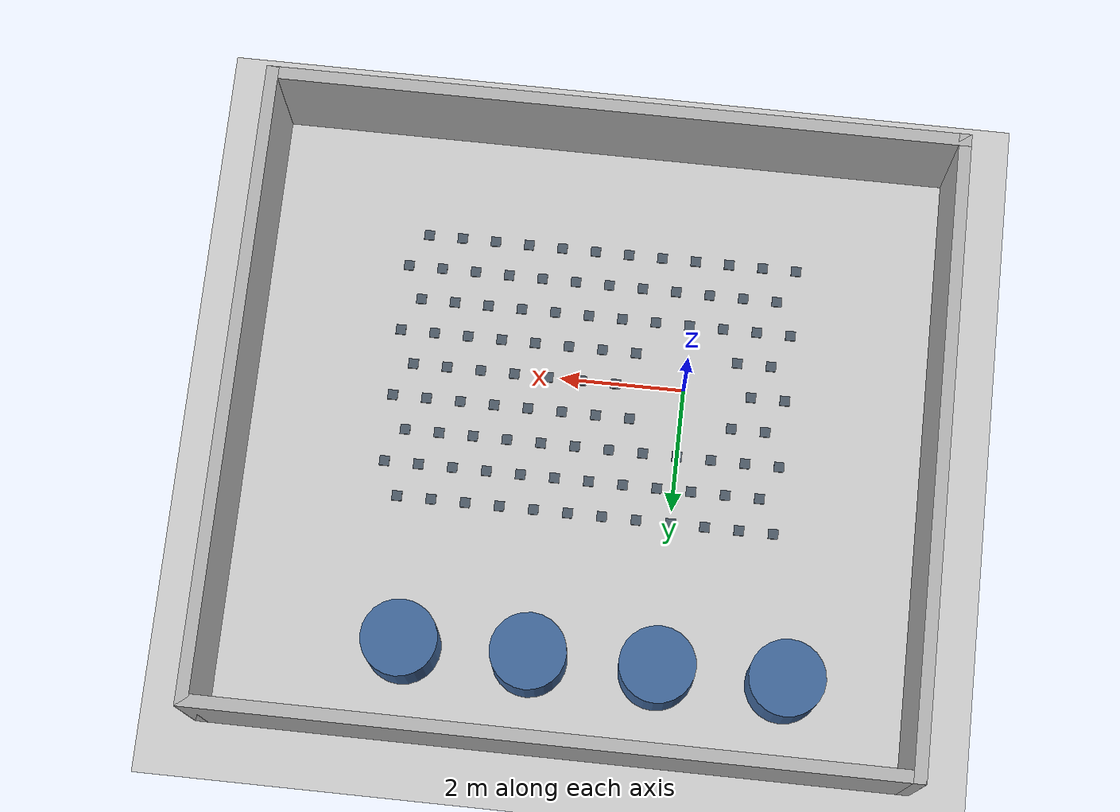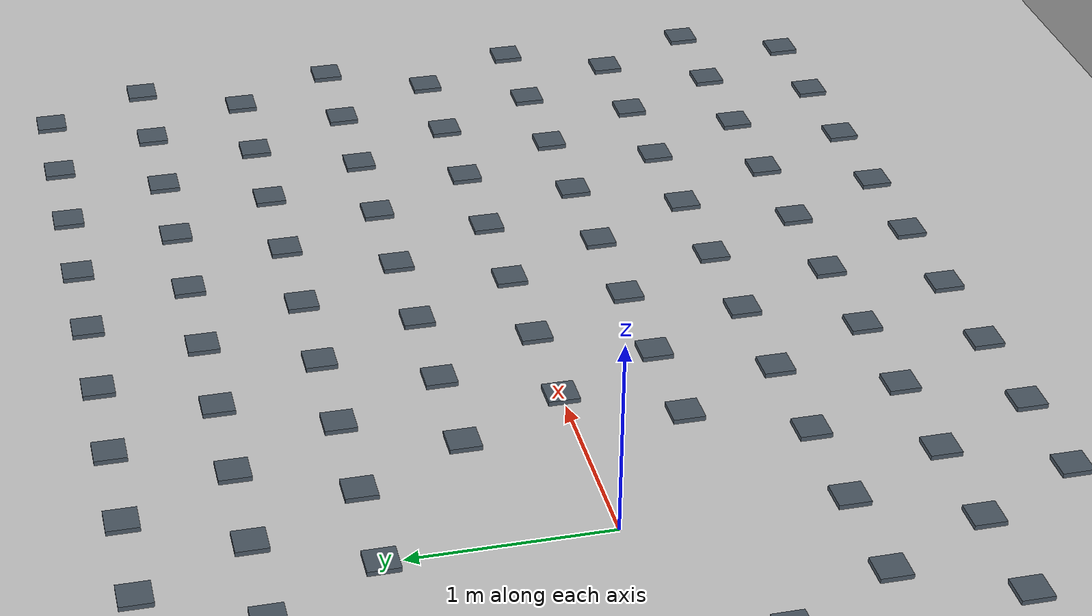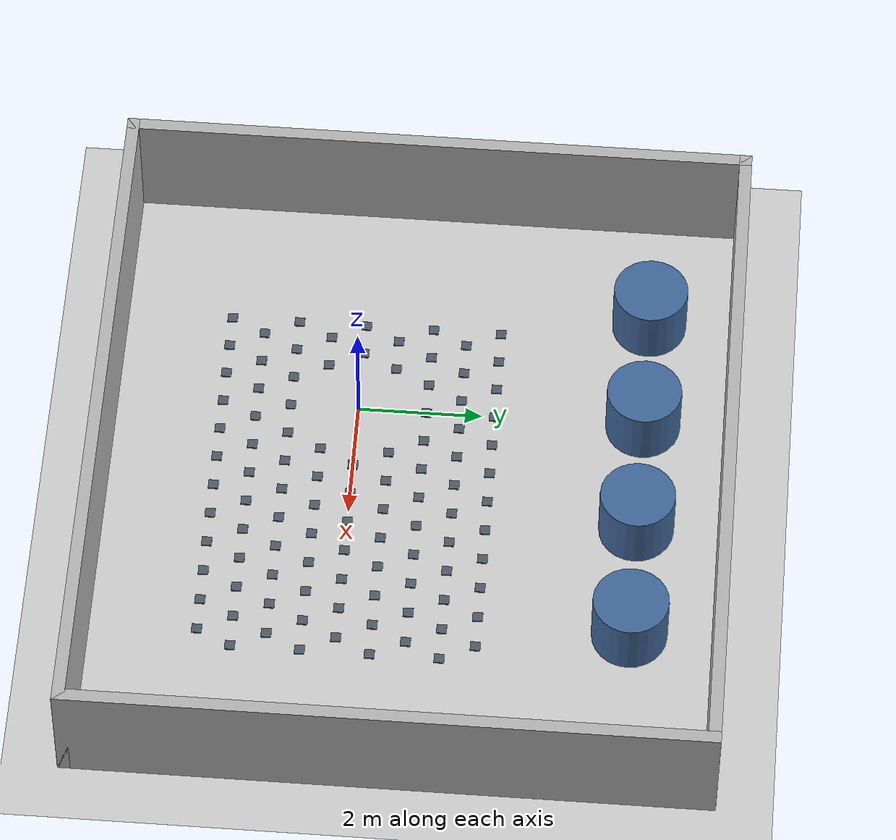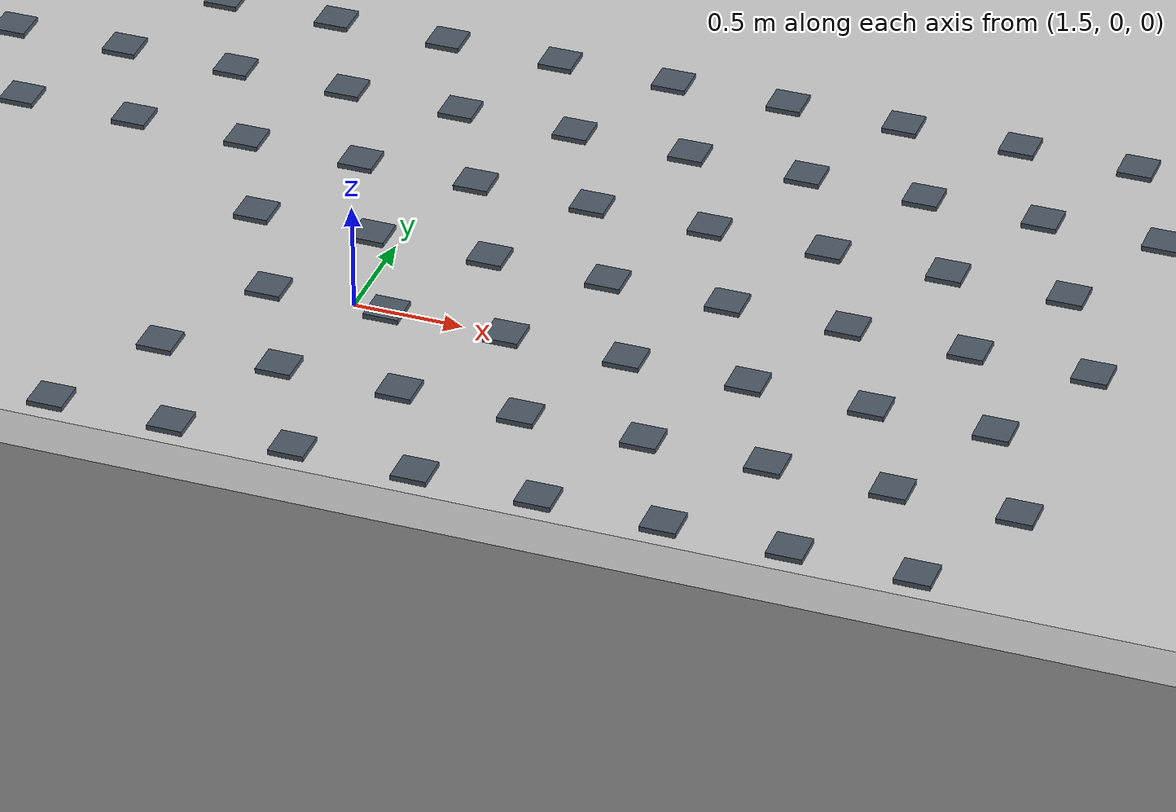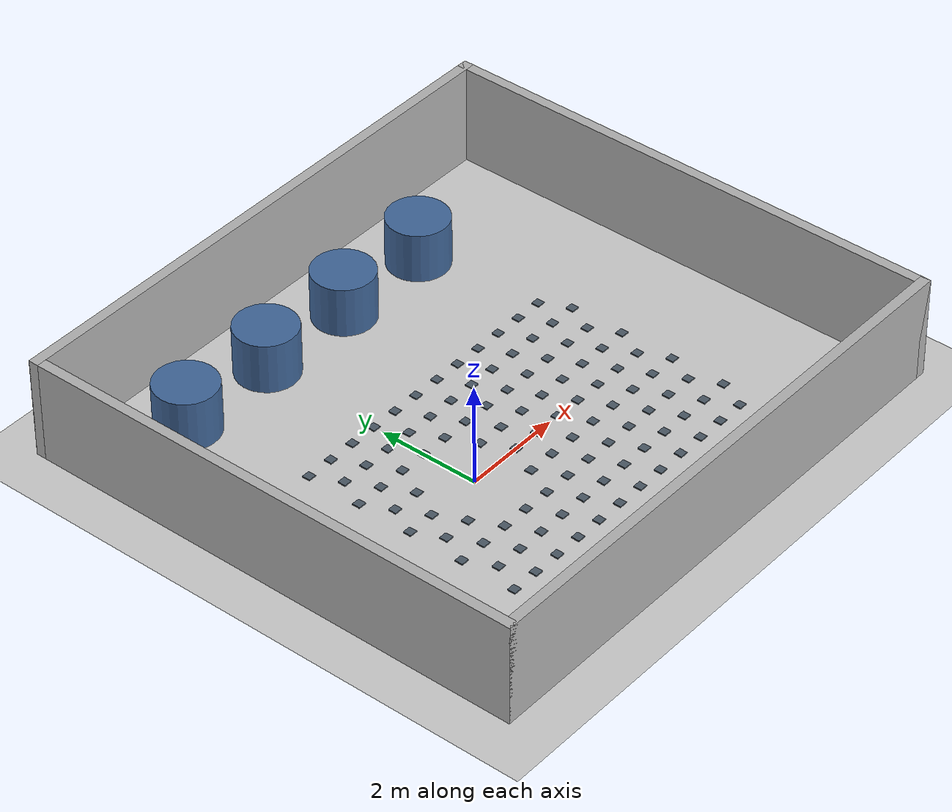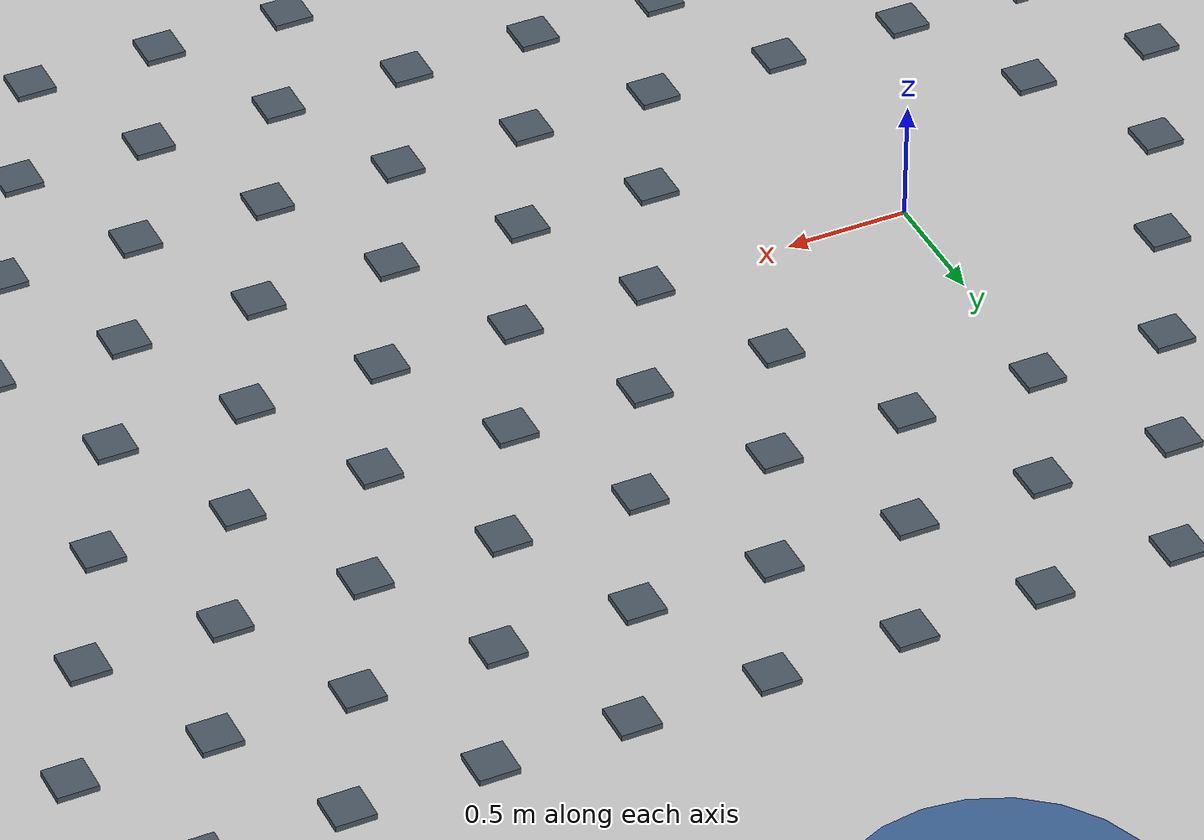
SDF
<?xml version="1.0" ?>
<!-- The rough_ground.sdf bump field, inside an 11 x 10 m walled room with a row of 4 round pillars, so lidar odometry has structure to match against. Generated by scripts/make_surface_worlds.py. -->
<sdf version="1.9">
  <world name="empty_ground">
    <physics name="1ms" type="ignored">
      <max_step_size>0.001</max_step_size>
      <real_time_factor>1.0</real_time_factor>
    </physics>
    <plugin filename="gz-sim-physics-system" name="gz::sim::systems::Physics"/>
    <plugin filename="gz-sim-user-commands-system" name="gz::sim::systems::UserCommands"/>
    <plugin filename="gz-sim-scene-broadcaster-system" name="gz::sim::systems::SceneBroadcaster"/>
    <plugin filename="gz-sim-sensors-system" name="gz::sim::systems::Sensors">
      <render_engine>ogre2</render_engine>
    </plugin>
    <plugin filename="gz-sim-imu-system" name="gz::sim::systems::Imu"/>

    <light type="directional" name="sun">
      <cast_shadows>true</cast_shadows>
      <pose>0 0 10 0 0 0</pose>
      <diffuse>0.8 0.8 0.8 1</diffuse>
      <specular>0.2 0.2 0.2 1</specular>
      <direction>-0.5 0.1 -0.9</direction>
    </light>

    <model name="ground_plane">
      <static>true</static>
      <link name="link">
        <collision name="collision">
          <geometry><plane><normal>0 0 1</normal><size>100 100</size></plane></geometry>
          <surface>
            <friction>
              <ode><mu>1.5</mu><mu2>1.5</mu2></ode>
              <torsional><coefficient>0.0</coefficient></torsional>
            </friction>
          </surface>
        </collision>
        <visual name="visual">
          <geometry><plane><normal>0 0 1</normal><size>100 100</size></plane></geometry>
          <material>
            <ambient>0.8 0.8 0.8 1</ambient>
            <diffuse>0.8 0.8 0.8 1</diffuse>
          </material>
        </visual>
      </link>
    </model>

    <model name="bump_1">
      <static>true</static>
      <pose>-1.650 -2.200 0.012 0 0 0</pose>
      <link name="link">
        <collision name="collision">
          <geometry><box><size>0.16 0.16 0.024</size></box></geometry>
          <surface>
            <friction>
              <ode><mu>1.5</mu><mu2>1.5</mu2></ode>
              <torsional><coefficient>0.0</coefficient></torsional>
            </friction>
          </surface>
        </collision>
        <visual name="visual">
          <geometry><box><size>0.16 0.16 0.024</size></box></geometry>
          <material>
            <ambient>0.25 0.3 0.35 1</ambient>
            <diffuse>0.30 0.35 0.4 1</diffuse>
          </material>
        </visual>
      </link>
    </model>

    <model name="bump_2">
      <static>true</static>
      <pose>-1.380 -1.650 0.012 0 0 0</pose>
      <link name="link">
        <collision name="collision">
          <geometry><box><size>0.16 0.16 0.024</size></box></geometry>
          <surface>
            <friction>
              <ode><mu>1.5</mu><mu2>1.5</mu2></ode>
              <torsional><coefficient>0.0</coefficient></torsional>
            </friction>
          </surface>
        </collision>
        <visual name="visual">
          <geometry><box><size>0.16 0.16 0.024</size></box></geometry>
          <material>
            <ambient>0.25 0.3 0.35 1</ambient>
            <diffuse>0.30 0.35 0.4 1</diffuse>
          </material>
        </visual>
      </link>
    </model>

    <model name="bump_3">
      <static>true</static>
      <pose>-1.650 -1.100 0.012 0 0 0</pose>
      <link name="link">
        <collision name="collision">
          <geometry><box><size>0.16 0.16 0.024</size></box></geometry>
          <surface>
            <friction>
              <ode><mu>1.5</mu><mu2>1.5</mu2></ode>
              <torsional><coefficient>0.0</coefficient></torsional>
            </friction>
          </surface>
        </collision>
        <visual name="visual">
          <geometry><box><size>0.16 0.16 0.024</size></box></geometry>
          <material>
            <ambient>0.25 0.3 0.35 1</ambient>
            <diffuse>0.30 0.35 0.4 1</diffuse>
          </material>
        </visual>
      </link>
    </model>

    <model name="bump_4">
      <static>true</static>
      <pose>-1.380 -0.550 0.012 0 0 0</pose>
      <link name="link">
        <collision name="collision">
          <geometry><box><size>0.16 0.16 0.024</size></box></geometry>
          <surface>
            <friction>
              <ode><mu>1.5</mu><mu2>1.5</mu2></ode>
              <torsional><coefficient>0.0</coefficient></torsional>
            </friction>
          </surface>
        </collision>
        <visual name="visual">
          <geometry><box><size>0.16 0.16 0.024</size></box></geometry>
          <material>
            <ambient>0.25 0.3 0.35 1</ambient>
            <diffuse>0.30 0.35 0.4 1</diffuse>
          </material>
        </visual>
      </link>
    </model>

    <model name="bump_5">
      <static>true</static>
      <pose>-1.650 0.000 0.012 0 0 0</pose>
      <link name="link">
        <collision name="collision">
          <geometry><box><size>0.16 0.16 0.024</size></box></geometry>
          <surface>
            <friction>
              <ode><mu>1.5</mu><mu2>1.5</mu2></ode>
              <torsional><coefficient>0.0</coefficient></torsional>
            </friction>
          </surface>
        </collision>
        <visual name="visual">
          <geometry><box><size>0.16 0.16 0.024</size></box></geometry>
          <material>
            <ambient>0.25 0.3 0.35 1</ambient>
            <diffuse>0.30 0.35 0.4 1</diffuse>
          </material>
        </visual>
      </link>
    </model>

    <model name="bump_6">
      <static>true</static>
      <pose>-1.380 0.550 0.012 0 0 0</pose>
      <link name="link">
        <collision name="collision">
          <geometry><box><size>0.16 0.16 0.024</size></box></geometry>
          <surface>
            <friction>
              <ode><mu>1.5</mu><mu2>1.5</mu2></ode>
              <torsional><coefficient>0.0</coefficient></torsional>
            </friction>
          </surface>
        </collision>
        <visual name="visual">
          <geometry><box><size>0.16 0.16 0.024</size></box></geometry>
          <material>
            <ambient>0.25 0.3 0.35 1</ambient>
            <diffuse>0.30 0.35 0.4 1</diffuse>
          </material>
        </visual>
      </link>
    </model>

    <model name="bump_7">
      <static>true</static>
      <pose>-1.650 1.100 0.012 0 0 0</pose>
      <link name="link">
        <collision name="collision">
          <geometry><box><size>0.16 0.16 0.024</size></box></geometry>
          <surface>
            <friction>
              <ode><mu>1.5</mu><mu2>1.5</mu2></ode>
              <torsional><coefficient>0.0</coefficient></torsional>
            </friction>
          </surface>
        </collision>
        <visual name="visual">
          <geometry><box><size>0.16 0.16 0.024</size></box></geometry>
          <material>
            <ambient>0.25 0.3 0.35 1</ambient>
            <diffuse>0.30 0.35 0.4 1</diffuse>
          </material>
        </visual>
      </link>
    </model>

    <model name="bump_8">
      <static>true</static>
      <pose>-1.380 1.650 0.012 0 0 0</pose>
      <link name="link">
        <collision name="collision">
          <geometry><box><size>0.16 0.16 0.024</size></box></geometry>
          <surface>
            <friction>
              <ode><mu>1.5</mu><mu2>1.5</mu2></ode>
              <torsional><coefficient>0.0</coefficient></torsional>
            </friction>
          </surface>
        </collision>
        <visual name="visual">
          <geometry><box><size>0.16 0.16 0.024</size></box></geometry>
          <material>
            <ambient>0.25 0.3 0.35 1</ambient>
            <diffuse>0.30 0.35 0.4 1</diffuse>
          </material>
        </visual>
      </link>
    </model>

    <model name="bump_9">
      <static>true</static>
      <pose>-1.650 2.200 0.012 0 0 0</pose>
      <link name="link">
        <collision name="collision">
          <geometry><box><size>0.16 0.16 0.024</size></box></geometry>
          <surface>
            <friction>
              <ode><mu>1.5</mu><mu2>1.5</mu2></ode>
              <torsional><coefficient>0.0</coefficient></torsional>
            </friction>
          </surface>
        </collision>
        <visual name="visual">
          <geometry><box><size>0.16 0.16 0.024</size></box></geometry>
          <material>
            <ambient>0.25 0.3 0.35 1</ambient>
            <diffuse>0.30 0.35 0.4 1</diffuse>
          </material>
        </visual>
      </link>
    </model>

    <model name="bump_10">
      <static>true</static>
      <pose>-1.100 -2.200 0.012 0 0 0</pose>
      <link name="link">
        <collision name="collision">
          <geometry><box><size>0.16 0.16 0.024</size></box></geometry>
          <surface>
            <friction>
              <ode><mu>1.5</mu><mu2>1.5</mu2></ode>
              <torsional><coefficient>0.0</coefficient></torsional>
            </friction>
          </surface>
        </collision>
        <visual name="visual">
          <geometry><box><size>0.16 0.16 0.024</size></box></geometry>
          <material>
            <ambient>0.25 0.3 0.35 1</ambient>
            <diffuse>0.30 0.35 0.4 1</diffuse>
          </material>
        </visual>
      </link>
    </model>

    <model name="bump_11">
      <static>true</static>
      <pose>-0.830 -1.650 0.012 0 0 0</pose>
      <link name="link">
        <collision name="collision">
          <geometry><box><size>0.16 0.16 0.024</size></box></geometry>
          <surface>
            <friction>
              <ode><mu>1.5</mu><mu2>1.5</mu2></ode>
              <torsional><coefficient>0.0</coefficient></torsional>
            </friction>
          </surface>
        </collision>
        <visual name="visual">
          <geometry><box><size>0.16 0.16 0.024</size></box></geometry>
          <material>
            <ambient>0.25 0.3 0.35 1</ambient>
            <diffuse>0.30 0.35 0.4 1</diffuse>
          </material>
        </visual>
      </link>
    </model>

    <model name="bump_12">
      <static>true</static>
      <pose>-1.100 -1.100 0.012 0 0 0</pose>
      <link name="link">
        <collision name="collision">
          <geometry><box><size>0.16 0.16 0.024</size></box></geometry>
          <surface>
            <friction>
              <ode><mu>1.5</mu><mu2>1.5</mu2></ode>
              <torsional><coefficient>0.0</coefficient></torsional>
            </friction>
          </surface>
        </collision>
        <visual name="visual">
          <geometry><box><size>0.16 0.16 0.024</size></box></geometry>
          <material>
            <ambient>0.25 0.3 0.35 1</ambient>
            <diffuse>0.30 0.35 0.4 1</diffuse>
          </material>
        </visual>
      </link>
    </model>

    <model name="bump_13">
      <static>true</static>
      <pose>-0.830 -0.550 0.012 0 0 0</pose>
      <link name="link">
        <collision name="collision">
          <geometry><box><size>0.16 0.16 0.024</size></box></geometry>
          <surface>
            <friction>
              <ode><mu>1.5</mu><mu2>1.5</mu2></ode>
              <torsional><coefficient>0.0</coefficient></torsional>
            </friction>
          </surface>
        </collision>
        <visual name="visual">
          <geometry><box><size>0.16 0.16 0.024</size></box></geometry>
          <material>
            <ambient>0.25 0.3 0.35 1</ambient>
            <diffuse>0.30 0.35 0.4 1</diffuse>
          </material>
        </visual>
      </link>
    </model>

    <model name="bump_14">
      <static>true</static>
      <pose>-1.100 0.000 0.012 0 0 0</pose>
      <link name="link">
        <collision name="collision">
          <geometry><box><size>0.16 0.16 0.024</size></box></geometry>
          <surface>
            <friction>
              <ode><mu>1.5</mu><mu2>1.5</mu2></ode>
              <torsional><coefficient>0.0</coefficient></torsional>
            </friction>
          </surface>
        </collision>
        <visual name="visual">
          <geometry><box><size>0.16 0.16 0.024</size></box></geometry>
          <material>
            <ambient>0.25 0.3 0.35 1</ambient>
            <diffuse>0.30 0.35 0.4 1</diffuse>
          </material>
        </visual>
      </link>
    </model>

    <model name="bump_15">
      <static>true</static>
      <pose>-0.830 0.550 0.012 0 0 0</pose>
      <link name="link">
        <collision name="collision">
          <geometry><box><size>0.16 0.16 0.024</size></box></geometry>
          <surface>
            <friction>
              <ode><mu>1.5</mu><mu2>1.5</mu2></ode>
              <torsional><coefficient>0.0</coefficient></torsional>
            </friction>
          </surface>
        </collision>
        <visual name="visual">
          <geometry><box><size>0.16 0.16 0.024</size></box></geometry>
          <material>
            <ambient>0.25 0.3 0.35 1</ambient>
            <diffuse>0.30 0.35 0.4 1</diffuse>
          </material>
        </visual>
      </link>
    </model>

    <model name="bump_16">
      <static>true</static>
      <pose>-1.100 1.100 0.012 0 0 0</pose>
      <link name="link">
        <collision name="collision">
          <geometry><box><size>0.16 0.16 0.024</size></box></geometry>
          <surface>
            <friction>
              <ode><mu>1.5</mu><mu2>1.5</mu2></ode>
              <torsional><coefficient>0.0</coefficient></torsional>
            </friction>
          </surface>
        </collision>
        <visual name="visual">
          <geometry><box><size>0.16 0.16 0.024</size></box></geometry>
          <material>
            <ambient>0.25 0.3 0.35 1</ambient>
            <diffuse>0.30 0.35 0.4 1</diffuse>
          </material>
        </visual>
      </link>
    </model>

    <model name="bump_17">
      <static>true</static>
      <pose>-0.830 1.650 0.012 0 0 0</pose>
      <link name="link">
        <collision name="collision">
          <geometry><box><size>0.16 0.16 0.024</size></box></geometry>
          <surface>
            <friction>
              <ode><mu>1.5</mu><mu2>1.5</mu2></ode>
              <torsional><coefficient>0.0</coefficient></torsional>
            </friction>
          </surface>
        </collision>
        <visual name="visual">
          <geometry><box><size>0.16 0.16 0.024</size></box></geometry>
          <material>
            <ambient>0.25 0.3 0.35 1</ambient>
            <diffuse>0.30 0.35 0.4 1</diffuse>
          </material>
        </visual>
      </link>
    </model>

    <model name="bump_18">
      <static>true</static>
      <pose>-1.100 2.200 0.012 0 0 0</pose>
      <link name="link">
        <collision name="collision">
          <geometry><box><size>0.16 0.16 0.024</size></box></geometry>
          <surface>
            <friction>
              <ode><mu>1.5</mu><mu2>1.5</mu2></ode>
              <torsional><coefficient>0.0</coefficient></torsional>
            </friction>
          </surface>
        </collision>
        <visual name="visual">
          <geometry><box><size>0.16 0.16 0.024</size></box></geometry>
          <material>
            <ambient>0.25 0.3 0.35 1</ambient>
            <diffuse>0.30 0.35 0.4 1</diffuse>
          </material>
        </visual>
      </link>
    </model>

    <model name="bump_19">
      <static>true</static>
      <pose>-0.550 -2.200 0.012 0 0 0</pose>
      <link name="link">
        <collision name="collision">
          <geometry><box><size>0.16 0.16 0.024</size></box></geometry>
          <surface>
            <friction>
              <ode><mu>1.5</mu><mu2>1.5</mu2></ode>
              <torsional><coefficient>0.0</coefficient></torsional>
            </friction>
          </surface>
        </collision>
        <visual name="visual">
          <geometry><box><size>0.16 0.16 0.024</size></box></geometry>
          <material>
            <ambient>0.25 0.3 0.35 1</ambient>
            <diffuse>0.30 0.35 0.4 1</diffuse>
          </material>
        </visual>
      </link>
    </model>

    <model name="bump_20">
      <static>true</static>
      <pose>-0.280 -1.650 0.012 0 0 0</pose>
      <link name="link">
        <collision name="collision">
          <geometry><box><size>0.16 0.16 0.024</size></box></geometry>
          <surface>
            <friction>
              <ode><mu>1.5</mu><mu2>1.5</mu2></ode>
              <torsional><coefficient>0.0</coefficient></torsional>
            </friction>
          </surface>
        </collision>
        <visual name="visual">
          <geometry><box><size>0.16 0.16 0.024</size></box></geometry>
          <material>
            <ambient>0.25 0.3 0.35 1</ambient>
            <diffuse>0.30 0.35 0.4 1</diffuse>
          </material>
        </visual>
      </link>
    </model>

    <model name="bump_21">
      <static>true</static>
      <pose>-0.550 -1.100 0.012 0 0 0</pose>
      <link name="link">
        <collision name="collision">
          <geometry><box><size>0.16 0.16 0.024</size></box></geometry>
          <surface>
            <friction>
              <ode><mu>1.5</mu><mu2>1.5</mu2></ode>
              <torsional><coefficient>0.0</coefficient></torsional>
            </friction>
          </surface>
        </collision>
        <visual name="visual">
          <geometry><box><size>0.16 0.16 0.024</size></box></geometry>
          <material>
            <ambient>0.25 0.3 0.35 1</ambient>
            <diffuse>0.30 0.35 0.4 1</diffuse>
          </material>
        </visual>
      </link>
    </model>

    <model name="bump_22">
      <static>true</static>
      <pose>-0.550 1.100 0.012 0 0 0</pose>
      <link name="link">
        <collision name="collision">
          <geometry><box><size>0.16 0.16 0.024</size></box></geometry>
          <surface>
            <friction>
              <ode><mu>1.5</mu><mu2>1.5</mu2></ode>
              <torsional><coefficient>0.0</coefficient></torsional>
            </friction>
          </surface>
        </collision>
        <visual name="visual">
          <geometry><box><size>0.16 0.16 0.024</size></box></geometry>
          <material>
            <ambient>0.25 0.3 0.35 1</ambient>
            <diffuse>0.30 0.35 0.4 1</diffuse>
          </material>
        </visual>
      </link>
    </model>

    <model name="bump_23">
      <static>true</static>
      <pose>-0.280 1.650 0.012 0 0 0</pose>
      <link name="link">
        <collision name="collision">
          <geometry><box><size>0.16 0.16 0.024</size></box></geometry>
          <surface>
            <friction>
              <ode><mu>1.5</mu><mu2>1.5</mu2></ode>
              <torsional><coefficient>0.0</coefficient></torsional>
            </friction>
          </surface>
        </collision>
        <visual name="visual">
          <geometry><box><size>0.16 0.16 0.024</size></box></geometry>
          <material>
            <ambient>0.25 0.3 0.35 1</ambient>
            <diffuse>0.30 0.35 0.4 1</diffuse>
          </material>
        </visual>
      </link>
    </model>

    <model name="bump_24">
      <static>true</static>
      <pose>-0.550 2.200 0.012 0 0 0</pose>
      <link name="link">
        <collision name="collision">
          <geometry><box><size>0.16 0.16 0.024</size></box></geometry>
          <surface>
            <friction>
              <ode><mu>1.5</mu><mu2>1.5</mu2></ode>
              <torsional><coefficient>0.0</coefficient></torsional>
            </friction>
          </surface>
        </collision>
        <visual name="visual">
          <geometry><box><size>0.16 0.16 0.024</size></box></geometry>
          <material>
            <ambient>0.25 0.3 0.35 1</ambient>
            <diffuse>0.30 0.35 0.4 1</diffuse>
          </material>
        </visual>
      </link>
    </model>

    <model name="bump_25">
      <static>true</static>
      <pose>0.000 -2.200 0.012 0 0 0</pose>
      <link name="link">
        <collision name="collision">
          <geometry><box><size>0.16 0.16 0.024</size></box></geometry>
          <surface>
            <friction>
              <ode><mu>1.5</mu><mu2>1.5</mu2></ode>
              <torsional><coefficient>0.0</coefficient></torsional>
            </friction>
          </surface>
        </collision>
        <visual name="visual">
          <geometry><box><size>0.16 0.16 0.024</size></box></geometry>
          <material>
            <ambient>0.25 0.3 0.35 1</ambient>
            <diffuse>0.30 0.35 0.4 1</diffuse>
          </material>
        </visual>
      </link>
    </model>

    <model name="bump_26">
      <static>true</static>
      <pose>0.270 -1.650 0.012 0 0 0</pose>
      <link name="link">
        <collision name="collision">
          <geometry><box><size>0.16 0.16 0.024</size></box></geometry>
          <surface>
            <friction>
              <ode><mu>1.5</mu><mu2>1.5</mu2></ode>
              <torsional><coefficient>0.0</coefficient></torsional>
            </friction>
          </surface>
        </collision>
        <visual name="visual">
          <geometry><box><size>0.16 0.16 0.024</size></box></geometry>
          <material>
            <ambient>0.25 0.3 0.35 1</ambient>
            <diffuse>0.30 0.35 0.4 1</diffuse>
          </material>
        </visual>
      </link>
    </model>

    <model name="bump_27">
      <static>true</static>
      <pose>0.000 -1.100 0.012 0 0 0</pose>
      <link name="link">
        <collision name="collision">
          <geometry><box><size>0.16 0.16 0.024</size></box></geometry>
          <surface>
            <friction>
              <ode><mu>1.5</mu><mu2>1.5</mu2></ode>
              <torsional><coefficient>0.0</coefficient></torsional>
            </friction>
          </surface>
        </collision>
        <visual name="visual">
          <geometry><box><size>0.16 0.16 0.024</size></box></geometry>
          <material>
            <ambient>0.25 0.3 0.35 1</ambient>
            <diffuse>0.30 0.35 0.4 1</diffuse>
          </material>
        </visual>
      </link>
    </model>

    <model name="bump_28">
      <static>true</static>
      <pose>0.000 1.100 0.012 0 0 0</pose>
      <link name="link">
        <collision name="collision">
          <geometry><box><size>0.16 0.16 0.024</size></box></geometry>
          <surface>
            <friction>
              <ode><mu>1.5</mu><mu2>1.5</mu2></ode>
              <torsional><coefficient>0.0</coefficient></torsional>
            </friction>
          </surface>
        </collision>
        <visual name="visual">
          <geometry><box><size>0.16 0.16 0.024</size></box></geometry>
          <material>
            <ambient>0.25 0.3 0.35 1</ambient>
            <diffuse>0.30 0.35 0.4 1</diffuse>
          </material>
        </visual>
      </link>
    </model>

    <model name="bump_29">
      <static>true</static>
      <pose>0.270 1.650 0.012 0 0 0</pose>
      <link name="link">
        <collision name="collision">
          <geometry><box><size>0.16 0.16 0.024</size></box></geometry>
          <surface>
            <friction>
              <ode><mu>1.5</mu><mu2>1.5</mu2></ode>
              <torsional><coefficient>0.0</coefficient></torsional>
            </friction>
          </surface>
        </collision>
        <visual name="visual">
          <geometry><box><size>0.16 0.16 0.024</size></box></geometry>
          <material>
            <ambient>0.25 0.3 0.35 1</ambient>
            <diffuse>0.30 0.35 0.4 1</diffuse>
          </material>
        </visual>
      </link>
    </model>

    <model name="bump_30">
      <static>true</static>
      <pose>0.000 2.200 0.012 0 0 0</pose>
      <link name="link">
        <collision name="collision">
          <geometry><box><size>0.16 0.16 0.024</size></box></geometry>
          <surface>
            <friction>
              <ode><mu>1.5</mu><mu2>1.5</mu2></ode>
              <torsional><coefficient>0.0</coefficient></torsional>
            </friction>
          </surface>
        </collision>
        <visual name="visual">
          <geometry><box><size>0.16 0.16 0.024</size></box></geometry>
          <material>
            <ambient>0.25 0.3 0.35 1</ambient>
            <diffuse>0.30 0.35 0.4 1</diffuse>
          </material>
        </visual>
      </link>
    </model>

    <model name="bump_31">
      <static>true</static>
      <pose>0.550 -2.200 0.012 0 0 0</pose>
      <link name="link">
        <collision name="collision">
          <geometry><box><size>0.16 0.16 0.024</size></box></geometry>
          <surface>
            <friction>
              <ode><mu>1.5</mu><mu2>1.5</mu2></ode>
              <torsional><coefficient>0.0</coefficient></torsional>
            </friction>
          </surface>
        </collision>
        <visual name="visual">
          <geometry><box><size>0.16 0.16 0.024</size></box></geometry>
          <material>
            <ambient>0.25 0.3 0.35 1</ambient>
            <diffuse>0.30 0.35 0.4 1</diffuse>
          </material>
        </visual>
      </link>
    </model>

    <model name="bump_32">
      <static>true</static>
      <pose>0.820 -1.650 0.012 0 0 0</pose>
      <link name="link">
        <collision name="collision">
          <geometry><box><size>0.16 0.16 0.024</size></box></geometry>
          <surface>
            <friction>
              <ode><mu>1.5</mu><mu2>1.5</mu2></ode>
              <torsional><coefficient>0.0</coefficient></torsional>
            </friction>
          </surface>
        </collision>
        <visual name="visual">
          <geometry><box><size>0.16 0.16 0.024</size></box></geometry>
          <material>
            <ambient>0.25 0.3 0.35 1</ambient>
            <diffuse>0.30 0.35 0.4 1</diffuse>
          </material>
        </visual>
      </link>
    </model>

    <model name="bump_33">
      <static>true</static>
      <pose>0.550 -1.100 0.012 0 0 0</pose>
      <link name="link">
        <collision name="collision">
          <geometry><box><size>0.16 0.16 0.024</size></box></geometry>
          <surface>
            <friction>
              <ode><mu>1.5</mu><mu2>1.5</mu2></ode>
              <torsional><coefficient>0.0</coefficient></torsional>
            </friction>
          </surface>
        </collision>
        <visual name="visual">
          <geometry><box><size>0.16 0.16 0.024</size></box></geometry>
          <material>
            <ambient>0.25 0.3 0.35 1</ambient>
            <diffuse>0.30 0.35 0.4 1</diffuse>
          </material>
        </visual>
      </link>
    </model>

    <model name="bump_34">
      <static>true</static>
      <pose>0.820 -0.550 0.012 0 0 0</pose>
      <link name="link">
        <collision name="collision">
          <geometry><box><size>0.16 0.16 0.024</size></box></geometry>
          <surface>
            <friction>
              <ode><mu>1.5</mu><mu2>1.5</mu2></ode>
              <torsional><coefficient>0.0</coefficient></torsional>
            </friction>
          </surface>
        </collision>
        <visual name="visual">
          <geometry><box><size>0.16 0.16 0.024</size></box></geometry>
          <material>
            <ambient>0.25 0.3 0.35 1</ambient>
            <diffuse>0.30 0.35 0.4 1</diffuse>
          </material>
        </visual>
      </link>
    </model>

    <model name="bump_35">
      <static>true</static>
      <pose>0.820 0.550 0.012 0 0 0</pose>
      <link name="link">
        <collision name="collision">
          <geometry><box><size>0.16 0.16 0.024</size></box></geometry>
          <surface>
            <friction>
              <ode><mu>1.5</mu><mu2>1.5</mu2></ode>
              <torsional><coefficient>0.0</coefficient></torsional>
            </friction>
          </surface>
        </collision>
        <visual name="visual">
          <geometry><box><size>0.16 0.16 0.024</size></box></geometry>
          <material>
            <ambient>0.25 0.3 0.35 1</ambient>
            <diffuse>0.30 0.35 0.4 1</diffuse>
          </material>
        </visual>
      </link>
    </model>

    <model name="bump_36">
      <static>true</static>
      <pose>0.550 1.100 0.012 0 0 0</pose>
      <link name="link">
        <collision name="collision">
          <geometry><box><size>0.16 0.16 0.024</size></box></geometry>
          <surface>
            <friction>
              <ode><mu>1.5</mu><mu2>1.5</mu2></ode>
              <torsional><coefficient>0.0</coefficient></torsional>
            </friction>
          </surface>
        </collision>
        <visual name="visual">
          <geometry><box><size>0.16 0.16 0.024</size></box></geometry>
          <material>
            <ambient>0.25 0.3 0.35 1</ambient>
            <diffuse>0.30 0.35 0.4 1</diffuse>
          </material>
        </visual>
      </link>
    </model>

    <model name="bump_37">
      <static>true</static>
      <pose>0.820 1.650 0.012 0 0 0</pose>
      <link name="link">
        <collision name="collision">
          <geometry><box><size>0.16 0.16 0.024</size></box></geometry>
          <surface>
            <friction>
              <ode><mu>1.5</mu><mu2>1.5</mu2></ode>
              <torsional><coefficient>0.0</coefficient></torsional>
            </friction>
          </surface>
        </collision>
        <visual name="visual">
          <geometry><box><size>0.16 0.16 0.024</size></box></geometry>
          <material>
            <ambient>0.25 0.3 0.35 1</ambient>
            <diffuse>0.30 0.35 0.4 1</diffuse>
          </material>
        </visual>
      </link>
    </model>

    <model name="bump_38">
      <static>true</static>
      <pose>0.550 2.200 0.012 0 0 0</pose>
      <link name="link">
        <collision name="collision">
          <geometry><box><size>0.16 0.16 0.024</size></box></geometry>
          <surface>
            <friction>
              <ode><mu>1.5</mu><mu2>1.5</mu2></ode>
              <torsional><coefficient>0.0</coefficient></torsional>
            </friction>
          </surface>
        </collision>
        <visual name="visual">
          <geometry><box><size>0.16 0.16 0.024</size></box></geometry>
          <material>
            <ambient>0.25 0.3 0.35 1</ambient>
            <diffuse>0.30 0.35 0.4 1</diffuse>
          </material>
        </visual>
      </link>
    </model>

    <model name="bump_39">
      <static>true</static>
      <pose>1.100 -2.200 0.012 0 0 0</pose>
      <link name="link">
        <collision name="collision">
          <geometry><box><size>0.16 0.16 0.024</size></box></geometry>
          <surface>
            <friction>
              <ode><mu>1.5</mu><mu2>1.5</mu2></ode>
              <torsional><coefficient>0.0</coefficient></torsional>
            </friction>
          </surface>
        </collision>
        <visual name="visual">
          <geometry><box><size>0.16 0.16 0.024</size></box></geometry>
          <material>
            <ambient>0.25 0.3 0.35 1</ambient>
            <diffuse>0.30 0.35 0.4 1</diffuse>
          </material>
        </visual>
      </link>
    </model>

    <model name="bump_40">
      <static>true</static>
      <pose>1.370 -1.650 0.012 0 0 0</pose>
      <link name="link">
        <collision name="collision">
          <geometry><box><size>0.16 0.16 0.024</size></box></geometry>
          <surface>
            <friction>
              <ode><mu>1.5</mu><mu2>1.5</mu2></ode>
              <torsional><coefficient>0.0</coefficient></torsional>
            </friction>
          </surface>
        </collision>
        <visual name="visual">
          <geometry><box><size>0.16 0.16 0.024</size></box></geometry>
          <material>
            <ambient>0.25 0.3 0.35 1</ambient>
            <diffuse>0.30 0.35 0.4 1</diffuse>
          </material>
        </visual>
      </link>
    </model>

    <model name="bump_41">
      <static>true</static>
      <pose>1.100 -1.100 0.012 0 0 0</pose>
      <link name="link">
        <collision name="collision">
          <geometry><box><size>0.16 0.16 0.024</size></box></geometry>
          <surface>
            <friction>
              <ode><mu>1.5</mu><mu2>1.5</mu2></ode>
              <torsional><coefficient>0.0</coefficient></torsional>
            </friction>
          </surface>
        </collision>
        <visual name="visual">
          <geometry><box><size>0.16 0.16 0.024</size></box></geometry>
          <material>
            <ambient>0.25 0.3 0.35 1</ambient>
            <diffuse>0.30 0.35 0.4 1</diffuse>
          </material>
        </visual>
      </link>
    </model>

    <model name="bump_42">
      <static>true</static>
      <pose>1.370 -0.550 0.012 0 0 0</pose>
      <link name="link">
        <collision name="collision">
          <geometry><box><size>0.16 0.16 0.024</size></box></geometry>
          <surface>
            <friction>
              <ode><mu>1.5</mu><mu2>1.5</mu2></ode>
              <torsional><coefficient>0.0</coefficient></torsional>
            </friction>
          </surface>
        </collision>
        <visual name="visual">
          <geometry><box><size>0.16 0.16 0.024</size></box></geometry>
          <material>
            <ambient>0.25 0.3 0.35 1</ambient>
            <diffuse>0.30 0.35 0.4 1</diffuse>
          </material>
        </visual>
      </link>
    </model>

    <model name="bump_43">
      <static>true</static>
      <pose>1.100 0.000 0.012 0 0 0</pose>
      <link name="link">
        <collision name="collision">
          <geometry><box><size>0.16 0.16 0.024</size></box></geometry>
          <surface>
            <friction>
              <ode><mu>1.5</mu><mu2>1.5</mu2></ode>
              <torsional><coefficient>0.0</coefficient></torsional>
            </friction>
          </surface>
        </collision>
        <visual name="visual">
          <geometry><box><size>0.16 0.16 0.024</size></box></geometry>
          <material>
            <ambient>0.25 0.3 0.35 1</ambient>
            <diffuse>0.30 0.35 0.4 1</diffuse>
          </material>
        </visual>
      </link>
    </model>

    <model name="bump_44">
      <static>true</static>
      <pose>1.370 0.550 0.012 0 0 0</pose>
      <link name="link">
        <collision name="collision">
          <geometry><box><size>0.16 0.16 0.024</size></box></geometry>
          <surface>
            <friction>
              <ode><mu>1.5</mu><mu2>1.5</mu2></ode>
              <torsional><coefficient>0.0</coefficient></torsional>
            </friction>
          </surface>
        </collision>
        <visual name="visual">
          <geometry><box><size>0.16 0.16 0.024</size></box></geometry>
          <material>
            <ambient>0.25 0.3 0.35 1</ambient>
            <diffuse>0.30 0.35 0.4 1</diffuse>
          </material>
        </visual>
      </link>
    </model>

    <model name="bump_45">
      <static>true</static>
      <pose>1.100 1.100 0.012 0 0 0</pose>
      <link name="link">
        <collision name="collision">
          <geometry><box><size>0.16 0.16 0.024</size></box></geometry>
          <surface>
            <friction>
              <ode><mu>1.5</mu><mu2>1.5</mu2></ode>
              <torsional><coefficient>0.0</coefficient></torsional>
            </friction>
          </surface>
        </collision>
        <visual name="visual">
          <geometry><box><size>0.16 0.16 0.024</size></box></geometry>
          <material>
            <ambient>0.25 0.3 0.35 1</ambient>
            <diffuse>0.30 0.35 0.4 1</diffuse>
          </material>
        </visual>
      </link>
    </model>

    <model name="bump_46">
      <static>true</static>
      <pose>1.370 1.650 0.012 0 0 0</pose>
      <link name="link">
        <collision name="collision">
          <geometry><box><size>0.16 0.16 0.024</size></box></geometry>
          <surface>
            <friction>
              <ode><mu>1.5</mu><mu2>1.5</mu2></ode>
              <torsional><coefficient>0.0</coefficient></torsional>
            </friction>
          </surface>
        </collision>
        <visual name="visual">
          <geometry><box><size>0.16 0.16 0.024</size></box></geometry>
          <material>
            <ambient>0.25 0.3 0.35 1</ambient>
            <diffuse>0.30 0.35 0.4 1</diffuse>
          </material>
        </visual>
      </link>
    </model>

    <model name="bump_47">
      <static>true</static>
      <pose>1.100 2.200 0.012 0 0 0</pose>
      <link name="link">
        <collision name="collision">
          <geometry><box><size>0.16 0.16 0.024</size></box></geometry>
          <surface>
            <friction>
              <ode><mu>1.5</mu><mu2>1.5</mu2></ode>
              <torsional><coefficient>0.0</coefficient></torsional>
            </friction>
          </surface>
        </collision>
        <visual name="visual">
          <geometry><box><size>0.16 0.16 0.024</size></box></geometry>
          <material>
            <ambient>0.25 0.3 0.35 1</ambient>
            <diffuse>0.30 0.35 0.4 1</diffuse>
          </material>
        </visual>
      </link>
    </model>

    <model name="bump_48">
      <static>true</static>
      <pose>1.650 -2.200 0.012 0 0 0</pose>
      <link name="link">
        <collision name="collision">
          <geometry><box><size>0.16 0.16 0.024</size></box></geometry>
          <surface>
            <friction>
              <ode><mu>1.5</mu><mu2>1.5</mu2></ode>
              <torsional><coefficient>0.0</coefficient></torsional>
            </friction>
          </surface>
        </collision>
        <visual name="visual">
          <geometry><box><size>0.16 0.16 0.024</size></box></geometry>
          <material>
            <ambient>0.25 0.3 0.35 1</ambient>
            <diffuse>0.30 0.35 0.4 1</diffuse>
          </material>
        </visual>
      </link>
    </model>

    <model name="bump_49">
      <static>true</static>
      <pose>1.920 -1.650 0.012 0 0 0</pose>
      <link name="link">
        <collision name="collision">
          <geometry><box><size>0.16 0.16 0.024</size></box></geometry>
          <surface>
            <friction>
              <ode><mu>1.5</mu><mu2>1.5</mu2></ode>
              <torsional><coefficient>0.0</coefficient></torsional>
            </friction>
          </surface>
        </collision>
        <visual name="visual">
          <geometry><box><size>0.16 0.16 0.024</size></box></geometry>
          <material>
            <ambient>0.25 0.3 0.35 1</ambient>
            <diffuse>0.30 0.35 0.4 1</diffuse>
          </material>
        </visual>
      </link>
    </model>

    <model name="bump_50">
      <static>true</static>
      <pose>1.650 -1.100 0.012 0 0 0</pose>
      <link name="link">
        <collision name="collision">
          <geometry><box><size>0.16 0.16 0.024</size></box></geometry>
          <surface>
            <friction>
              <ode><mu>1.5</mu><mu2>1.5</mu2></ode>
              <torsional><coefficient>0.0</coefficient></torsional>
            </friction>
          </surface>
        </collision>
        <visual name="visual">
          <geometry><box><size>0.16 0.16 0.024</size></box></geometry>
          <material>
            <ambient>0.25 0.3 0.35 1</ambient>
            <diffuse>0.30 0.35 0.4 1</diffuse>
          </material>
        </visual>
      </link>
    </model>

    <model name="bump_51">
      <static>true</static>
      <pose>1.920 -0.550 0.012 0 0 0</pose>
      <link name="link">
        <collision name="collision">
          <geometry><box><size>0.16 0.16 0.024</size></box></geometry>
          <surface>
            <friction>
              <ode><mu>1.5</mu><mu2>1.5</mu2></ode>
              <torsional><coefficient>0.0</coefficient></torsional>
            </friction>
          </surface>
        </collision>
        <visual name="visual">
          <geometry><box><size>0.16 0.16 0.024</size></box></geometry>
          <material>
            <ambient>0.25 0.3 0.35 1</ambient>
            <diffuse>0.30 0.35 0.4 1</diffuse>
          </material>
        </visual>
      </link>
    </model>

    <model name="bump_52">
      <static>true</static>
      <pose>1.650 0.000 0.012 0 0 0</pose>
      <link name="link">
        <collision name="collision">
          <geometry><box><size>0.16 0.16 0.024</size></box></geometry>
          <surface>
            <friction>
              <ode><mu>1.5</mu><mu2>1.5</mu2></ode>
              <torsional><coefficient>0.0</coefficient></torsional>
            </friction>
          </surface>
        </collision>
        <visual name="visual">
          <geometry><box><size>0.16 0.16 0.024</size></box></geometry>
          <material>
            <ambient>0.25 0.3 0.35 1</ambient>
            <diffuse>0.30 0.35 0.4 1</diffuse>
          </material>
        </visual>
      </link>
    </model>

    <model name="bump_53">
      <static>true</static>
      <pose>1.920 0.550 0.012 0 0 0</pose>
      <link name="link">
        <collision name="collision">
          <geometry><box><size>0.16 0.16 0.024</size></box></geometry>
          <surface>
            <friction>
              <ode><mu>1.5</mu><mu2>1.5</mu2></ode>
              <torsional><coefficient>0.0</coefficient></torsional>
            </friction>
          </surface>
        </collision>
        <visual name="visual">
          <geometry><box><size>0.16 0.16 0.024</size></box></geometry>
          <material>
            <ambient>0.25 0.3 0.35 1</ambient>
            <diffuse>0.30 0.35 0.4 1</diffuse>
          </material>
        </visual>
      </link>
    </model>

    <model name="bump_54">
      <static>true</static>
      <pose>1.650 1.100 0.012 0 0 0</pose>
      <link name="link">
        <collision name="collision">
          <geometry><box><size>0.16 0.16 0.024</size></box></geometry>
          <surface>
            <friction>
              <ode><mu>1.5</mu><mu2>1.5</mu2></ode>
              <torsional><coefficient>0.0</coefficient></torsional>
            </friction>
          </surface>
        </collision>
        <visual name="visual">
          <geometry><box><size>0.16 0.16 0.024</size></box></geometry>
          <material>
            <ambient>0.25 0.3 0.35 1</ambient>
            <diffuse>0.30 0.35 0.4 1</diffuse>
          </material>
        </visual>
      </link>
    </model>

    <model name="bump_55">
      <static>true</static>
      <pose>1.920 1.650 0.012 0 0 0</pose>
      <link name="link">
        <collision name="collision">
          <geometry><box><size>0.16 0.16 0.024</size></box></geometry>
          <surface>
            <friction>
              <ode><mu>1.5</mu><mu2>1.5</mu2></ode>
              <torsional><coefficient>0.0</coefficient></torsional>
            </friction>
          </surface>
        </collision>
        <visual name="visual">
          <geometry><box><size>0.16 0.16 0.024</size></box></geometry>
          <material>
            <ambient>0.25 0.3 0.35 1</ambient>
            <diffuse>0.30 0.35 0.4 1</diffuse>
          </material>
        </visual>
      </link>
    </model>

    <model name="bump_56">
      <static>true</static>
      <pose>1.650 2.200 0.012 0 0 0</pose>
      <link name="link">
        <collision name="collision">
          <geometry><box><size>0.16 0.16 0.024</size></box></geometry>
          <surface>
            <friction>
              <ode><mu>1.5</mu><mu2>1.5</mu2></ode>
              <torsional><coefficient>0.0</coefficient></torsional>
            </friction>
          </surface>
        </collision>
        <visual name="visual">
          <geometry><box><size>0.16 0.16 0.024</size></box></geometry>
          <material>
            <ambient>0.25 0.3 0.35 1</ambient>
            <diffuse>0.30 0.35 0.4 1</diffuse>
          </material>
        </visual>
      </link>
    </model>

    <model name="bump_57">
      <static>true</static>
      <pose>2.200 -2.200 0.012 0 0 0</pose>
      <link name="link">
        <collision name="collision">
          <geometry><box><size>0.16 0.16 0.024</size></box></geometry>
          <surface>
            <friction>
              <ode><mu>1.5</mu><mu2>1.5</mu2></ode>
              <torsional><coefficient>0.0</coefficient></torsional>
            </friction>
          </surface>
        </collision>
        <visual name="visual">
          <geometry><box><size>0.16 0.16 0.024</size></box></geometry>
          <material>
            <ambient>0.25 0.3 0.35 1</ambient>
            <diffuse>0.30 0.35 0.4 1</diffuse>
          </material>
        </visual>
      </link>
    </model>

    <model name="bump_58">
      <static>true</static>
      <pose>2.470 -1.650 0.012 0 0 0</pose>
      <link name="link">
        <collision name="collision">
          <geometry><box><size>0.16 0.16 0.024</size></box></geometry>
          <surface>
            <friction>
              <ode><mu>1.5</mu><mu2>1.5</mu2></ode>
              <torsional><coefficient>0.0</coefficient></torsional>
            </friction>
          </surface>
        </collision>
        <visual name="visual">
          <geometry><box><size>0.16 0.16 0.024</size></box></geometry>
          <material>
            <ambient>0.25 0.3 0.35 1</ambient>
            <diffuse>0.30 0.35 0.4 1</diffuse>
          </material>
        </visual>
      </link>
    </model>

    <model name="bump_59">
      <static>true</static>
      <pose>2.200 -1.100 0.012 0 0 0</pose>
      <link name="link">
        <collision name="collision">
          <geometry><box><size>0.16 0.16 0.024</size></box></geometry>
          <surface>
            <friction>
              <ode><mu>1.5</mu><mu2>1.5</mu2></ode>
              <torsional><coefficient>0.0</coefficient></torsional>
            </friction>
          </surface>
        </collision>
        <visual name="visual">
          <geometry><box><size>0.16 0.16 0.024</size></box></geometry>
          <material>
            <ambient>0.25 0.3 0.35 1</ambient>
            <diffuse>0.30 0.35 0.4 1</diffuse>
          </material>
        </visual>
      </link>
    </model>

    <model name="bump_60">
      <static>true</static>
      <pose>2.470 -0.550 0.012 0 0 0</pose>
      <link name="link">
        <collision name="collision">
          <geometry><box><size>0.16 0.16 0.024</size></box></geometry>
          <surface>
            <friction>
              <ode><mu>1.5</mu><mu2>1.5</mu2></ode>
              <torsional><coefficient>0.0</coefficient></torsional>
            </friction>
          </surface>
        </collision>
        <visual name="visual">
          <geometry><box><size>0.16 0.16 0.024</size></box></geometry>
          <material>
            <ambient>0.25 0.3 0.35 1</ambient>
            <diffuse>0.30 0.35 0.4 1</diffuse>
          </material>
        </visual>
      </link>
    </model>

    <model name="bump_61">
      <static>true</static>
      <pose>2.200 0.000 0.012 0 0 0</pose>
      <link name="link">
        <collision name="collision">
          <geometry><box><size>0.16 0.16 0.024</size></box></geometry>
          <surface>
            <friction>
              <ode><mu>1.5</mu><mu2>1.5</mu2></ode>
              <torsional><coefficient>0.0</coefficient></torsional>
            </friction>
          </surface>
        </collision>
        <visual name="visual">
          <geometry><box><size>0.16 0.16 0.024</size></box></geometry>
          <material>
            <ambient>0.25 0.3 0.35 1</ambient>
            <diffuse>0.30 0.35 0.4 1</diffuse>
          </material>
        </visual>
      </link>
    </model>

    <model name="bump_62">
      <static>true</static>
      <pose>2.470 0.550 0.012 0 0 0</pose>
      <link name="link">
        <collision name="collision">
          <geometry><box><size>0.16 0.16 0.024</size></box></geometry>
          <surface>
            <friction>
              <ode><mu>1.5</mu><mu2>1.5</mu2></ode>
              <torsional><coefficient>0.0</coefficient></torsional>
            </friction>
          </surface>
        </collision>
        <visual name="visual">
          <geometry><box><size>0.16 0.16 0.024</size></box></geometry>
          <material>
            <ambient>0.25 0.3 0.35 1</ambient>
            <diffuse>0.30 0.35 0.4 1</diffuse>
          </material>
        </visual>
      </link>
    </model>

    <model name="bump_63">
      <static>true</static>
      <pose>2.200 1.100 0.012 0 0 0</pose>
      <link name="link">
        <collision name="collision">
          <geometry><box><size>0.16 0.16 0.024</size></box></geometry>
          <surface>
            <friction>
              <ode><mu>1.5</mu><mu2>1.5</mu2></ode>
              <torsional><coefficient>0.0</coefficient></torsional>
            </friction>
          </surface>
        </collision>
        <visual name="visual">
          <geometry><box><size>0.16 0.16 0.024</size></box></geometry>
          <material>
            <ambient>0.25 0.3 0.35 1</ambient>
            <diffuse>0.30 0.35 0.4 1</diffuse>
          </material>
        </visual>
      </link>
    </model>

    <model name="bump_64">
      <static>true</static>
      <pose>2.470 1.650 0.012 0 0 0</pose>
      <link name="link">
        <collision name="collision">
          <geometry><box><size>0.16 0.16 0.024</size></box></geometry>
          <surface>
            <friction>
              <ode><mu>1.5</mu><mu2>1.5</mu2></ode>
              <torsional><coefficient>0.0</coefficient></torsional>
            </friction>
          </surface>
        </collision>
        <visual name="visual">
          <geometry><box><size>0.16 0.16 0.024</size></box></geometry>
          <material>
            <ambient>0.25 0.3 0.35 1</ambient>
            <diffuse>0.30 0.35 0.4 1</diffuse>
          </material>
        </visual>
      </link>
    </model>

    <model name="bump_65">
      <static>true</static>
      <pose>2.200 2.200 0.012 0 0 0</pose>
      <link name="link">
        <collision name="collision">
          <geometry><box><size>0.16 0.16 0.024</size></box></geometry>
          <surface>
            <friction>
              <ode><mu>1.5</mu><mu2>1.5</mu2></ode>
              <torsional><coefficient>0.0</coefficient></torsional>
            </friction>
          </surface>
        </collision>
        <visual name="visual">
          <geometry><box><size>0.16 0.16 0.024</size></box></geometry>
          <material>
            <ambient>0.25 0.3 0.35 1</ambient>
            <diffuse>0.30 0.35 0.4 1</diffuse>
          </material>
        </visual>
      </link>
    </model>

    <model name="bump_66">
      <static>true</static>
      <pose>2.750 -2.200 0.012 0 0 0</pose>
      <link name="link">
        <collision name="collision">
          <geometry><box><size>0.16 0.16 0.024</size></box></geometry>
          <surface>
            <friction>
              <ode><mu>1.5</mu><mu2>1.5</mu2></ode>
              <torsional><coefficient>0.0</coefficient></torsional>
            </friction>
          </surface>
        </collision>
        <visual name="visual">
          <geometry><box><size>0.16 0.16 0.024</size></box></geometry>
          <material>
            <ambient>0.25 0.3 0.35 1</ambient>
            <diffuse>0.30 0.35 0.4 1</diffuse>
          </material>
        </visual>
      </link>
    </model>

    <model name="bump_67">
      <static>true</static>
      <pose>3.020 -1.650 0.012 0 0 0</pose>
      <link name="link">
        <collision name="collision">
          <geometry><box><size>0.16 0.16 0.024</size></box></geometry>
          <surface>
            <friction>
              <ode><mu>1.5</mu><mu2>1.5</mu2></ode>
              <torsional><coefficient>0.0</coefficient></torsional>
            </friction>
          </surface>
        </collision>
        <visual name="visual">
          <geometry><box><size>0.16 0.16 0.024</size></box></geometry>
          <material>
            <ambient>0.25 0.3 0.35 1</ambient>
            <diffuse>0.30 0.35 0.4 1</diffuse>
          </material>
        </visual>
      </link>
    </model>

    <model name="bump_68">
      <static>true</static>
      <pose>2.750 -1.100 0.012 0 0 0</pose>
      <link name="link">
        <collision name="collision">
          <geometry><box><size>0.16 0.16 0.024</size></box></geometry>
          <surface>
            <friction>
              <ode><mu>1.5</mu><mu2>1.5</mu2></ode>
              <torsional><coefficient>0.0</coefficient></torsional>
            </friction>
          </surface>
        </collision>
        <visual name="visual">
          <geometry><box><size>0.16 0.16 0.024</size></box></geometry>
          <material>
            <ambient>0.25 0.3 0.35 1</ambient>
            <diffuse>0.30 0.35 0.4 1</diffuse>
          </material>
        </visual>
      </link>
    </model>

    <model name="bump_69">
      <static>true</static>
      <pose>3.020 -0.550 0.012 0 0 0</pose>
      <link name="link">
        <collision name="collision">
          <geometry><box><size>0.16 0.16 0.024</size></box></geometry>
          <surface>
            <friction>
              <ode><mu>1.5</mu><mu2>1.5</mu2></ode>
              <torsional><coefficient>0.0</coefficient></torsional>
            </friction>
          </surface>
        </collision>
        <visual name="visual">
          <geometry><box><size>0.16 0.16 0.024</size></box></geometry>
          <material>
            <ambient>0.25 0.3 0.35 1</ambient>
            <diffuse>0.30 0.35 0.4 1</diffuse>
          </material>
        </visual>
      </link>
    </model>

    <model name="bump_70">
      <static>true</static>
      <pose>2.750 0.000 0.012 0 0 0</pose>
      <link name="link">
        <collision name="collision">
          <geometry><box><size>0.16 0.16 0.024</size></box></geometry>
          <surface>
            <friction>
              <ode><mu>1.5</mu><mu2>1.5</mu2></ode>
              <torsional><coefficient>0.0</coefficient></torsional>
            </friction>
          </surface>
        </collision>
        <visual name="visual">
          <geometry><box><size>0.16 0.16 0.024</size></box></geometry>
          <material>
            <ambient>0.25 0.3 0.35 1</ambient>
            <diffuse>0.30 0.35 0.4 1</diffuse>
          </material>
        </visual>
      </link>
    </model>

    <model name="bump_71">
      <static>true</static>
      <pose>3.020 0.550 0.012 0 0 0</pose>
      <link name="link">
        <collision name="collision">
          <geometry><box><size>0.16 0.16 0.024</size></box></geometry>
          <surface>
            <friction>
              <ode><mu>1.5</mu><mu2>1.5</mu2></ode>
              <torsional><coefficient>0.0</coefficient></torsional>
            </friction>
          </surface>
        </collision>
        <visual name="visual">
          <geometry><box><size>0.16 0.16 0.024</size></box></geometry>
          <material>
            <ambient>0.25 0.3 0.35 1</ambient>
            <diffuse>0.30 0.35 0.4 1</diffuse>
          </material>
        </visual>
      </link>
    </model>

    <model name="bump_72">
      <static>true</static>
      <pose>2.750 1.100 0.012 0 0 0</pose>
      <link name="link">
        <collision name="collision">
          <geometry><box><size>0.16 0.16 0.024</size></box></geometry>
          <surface>
            <friction>
              <ode><mu>1.5</mu><mu2>1.5</mu2></ode>
              <torsional><coefficient>0.0</coefficient></torsional>
            </friction>
          </surface>
        </collision>
        <visual name="visual">
          <geometry><box><size>0.16 0.16 0.024</size></box></geometry>
          <material>
            <ambient>0.25 0.3 0.35 1</ambient>
            <diffuse>0.30 0.35 0.4 1</diffuse>
          </material>
        </visual>
      </link>
    </model>

    <model name="bump_73">
      <static>true</static>
      <pose>3.020 1.650 0.012 0 0 0</pose>
      <link name="link">
        <collision name="collision">
          <geometry><box><size>0.16 0.16 0.024</size></box></geometry>
          <surface>
            <friction>
              <ode><mu>1.5</mu><mu2>1.5</mu2></ode>
              <torsional><coefficient>0.0</coefficient></torsional>
            </friction>
          </surface>
        </collision>
        <visual name="visual">
          <geometry><box><size>0.16 0.16 0.024</size></box></geometry>
          <material>
            <ambient>0.25 0.3 0.35 1</ambient>
            <diffuse>0.30 0.35 0.4 1</diffuse>
          </material>
        </visual>
      </link>
    </model>

    <model name="bump_74">
      <static>true</static>
      <pose>2.750 2.200 0.012 0 0 0</pose>
      <link name="link">
        <collision name="collision">
          <geometry><box><size>0.16 0.16 0.024</size></box></geometry>
          <surface>
            <friction>
              <ode><mu>1.5</mu><mu2>1.5</mu2></ode>
              <torsional><coefficient>0.0</coefficient></torsional>
            </friction>
          </surface>
        </collision>
        <visual name="visual">
          <geometry><box><size>0.16 0.16 0.024</size></box></geometry>
          <material>
            <ambient>0.25 0.3 0.35 1</ambient>
            <diffuse>0.30 0.35 0.4 1</diffuse>
          </material>
        </visual>
      </link>
    </model>

    <model name="bump_75">
      <static>true</static>
      <pose>3.300 -2.200 0.012 0 0 0</pose>
      <link name="link">
        <collision name="collision">
          <geometry><box><size>0.16 0.16 0.024</size></box></geometry>
          <surface>
            <friction>
              <ode><mu>1.5</mu><mu2>1.5</mu2></ode>
              <torsional><coefficient>0.0</coefficient></torsional>
            </friction>
          </surface>
        </collision>
        <visual name="visual">
          <geometry><box><size>0.16 0.16 0.024</size></box></geometry>
          <material>
            <ambient>0.25 0.3 0.35 1</ambient>
            <diffuse>0.30 0.35 0.4 1</diffuse>
          </material>
        </visual>
      </link>
    </model>

    <model name="bump_76">
      <static>true</static>
      <pose>3.570 -1.650 0.012 0 0 0</pose>
      <link name="link">
        <collision name="collision">
          <geometry><box><size>0.16 0.16 0.024</size></box></geometry>
          <surface>
            <friction>
              <ode><mu>1.5</mu><mu2>1.5</mu2></ode>
              <torsional><coefficient>0.0</coefficient></torsional>
            </friction>
          </surface>
        </collision>
        <visual name="visual">
          <geometry><box><size>0.16 0.16 0.024</size></box></geometry>
          <material>
            <ambient>0.25 0.3 0.35 1</ambient>
            <diffuse>0.30 0.35 0.4 1</diffuse>
          </material>
        </visual>
      </link>
    </model>

    <model name="bump_77">
      <static>true</static>
      <pose>3.300 -1.100 0.012 0 0 0</pose>
      <link name="link">
        <collision name="collision">
          <geometry><box><size>0.16 0.16 0.024</size></box></geometry>
          <surface>
            <friction>
              <ode><mu>1.5</mu><mu2>1.5</mu2></ode>
              <torsional><coefficient>0.0</coefficient></torsional>
            </friction>
          </surface>
        </collision>
        <visual name="visual">
          <geometry><box><size>0.16 0.16 0.024</size></box></geometry>
          <material>
            <ambient>0.25 0.3 0.35 1</ambient>
            <diffuse>0.30 0.35 0.4 1</diffuse>
          </material>
        </visual>
      </link>
    </model>

    <model name="bump_78">
      <static>true</static>
      <pose>3.570 -0.550 0.012 0 0 0</pose>
      <link name="link">
        <collision name="collision">
          <geometry><box><size>0.16 0.16 0.024</size></box></geometry>
          <surface>
            <friction>
              <ode><mu>1.5</mu><mu2>1.5</mu2></ode>
              <torsional><coefficient>0.0</coefficient></torsional>
            </friction>
          </surface>
        </collision>
        <visual name="visual">
          <geometry><box><size>0.16 0.16 0.024</size></box></geometry>
          <material>
            <ambient>0.25 0.3 0.35 1</ambient>
            <diffuse>0.30 0.35 0.4 1</diffuse>
          </material>
        </visual>
      </link>
    </model>

    <model name="bump_79">
      <static>true</static>
      <pose>3.300 0.000 0.012 0 0 0</pose>
      <link name="link">
        <collision name="collision">
          <geometry><box><size>0.16 0.16 0.024</size></box></geometry>
          <surface>
            <friction>
              <ode><mu>1.5</mu><mu2>1.5</mu2></ode>
              <torsional><coefficient>0.0</coefficient></torsional>
            </friction>
          </surface>
        </collision>
        <visual name="visual">
          <geometry><box><size>0.16 0.16 0.024</size></box></geometry>
          <material>
            <ambient>0.25 0.3 0.35 1</ambient>
            <diffuse>0.30 0.35 0.4 1</diffuse>
          </material>
        </visual>
      </link>
    </model>

    <model name="bump_80">
      <static>true</static>
      <pose>3.570 0.550 0.012 0 0 0</pose>
      <link name="link">
        <collision name="collision">
          <geometry><box><size>0.16 0.16 0.024</size></box></geometry>
          <surface>
            <friction>
              <ode><mu>1.5</mu><mu2>1.5</mu2></ode>
              <torsional><coefficient>0.0</coefficient></torsional>
            </friction>
          </surface>
        </collision>
        <visual name="visual">
          <geometry><box><size>0.16 0.16 0.024</size></box></geometry>
          <material>
            <ambient>0.25 0.3 0.35 1</ambient>
            <diffuse>0.30 0.35 0.4 1</diffuse>
          </material>
        </visual>
      </link>
    </model>

    <model name="bump_81">
      <static>true</static>
      <pose>3.300 1.100 0.012 0 0 0</pose>
      <link name="link">
        <collision name="collision">
          <geometry><box><size>0.16 0.16 0.024</size></box></geometry>
          <surface>
            <friction>
              <ode><mu>1.5</mu><mu2>1.5</mu2></ode>
              <torsional><coefficient>0.0</coefficient></torsional>
            </friction>
          </surface>
        </collision>
        <visual name="visual">
          <geometry><box><size>0.16 0.16 0.024</size></box></geometry>
          <material>
            <ambient>0.25 0.3 0.35 1</ambient>
            <diffuse>0.30 0.35 0.4 1</diffuse>
          </material>
        </visual>
      </link>
    </model>

    <model name="bump_82">
      <static>true</static>
      <pose>3.570 1.650 0.012 0 0 0</pose>
      <link name="link">
        <collision name="collision">
          <geometry><box><size>0.16 0.16 0.024</size></box></geometry>
          <surface>
            <friction>
              <ode><mu>1.5</mu><mu2>1.5</mu2></ode>
              <torsional><coefficient>0.0</coefficient></torsional>
            </friction>
          </surface>
        </collision>
        <visual name="visual">
          <geometry><box><size>0.16 0.16 0.024</size></box></geometry>
          <material>
            <ambient>0.25 0.3 0.35 1</ambient>
            <diffuse>0.30 0.35 0.4 1</diffuse>
          </material>
        </visual>
      </link>
    </model>

    <model name="bump_83">
      <static>true</static>
      <pose>3.300 2.200 0.012 0 0 0</pose>
      <link name="link">
        <collision name="collision">
          <geometry><box><size>0.16 0.16 0.024</size></box></geometry>
          <surface>
            <friction>
              <ode><mu>1.5</mu><mu2>1.5</mu2></ode>
              <torsional><coefficient>0.0</coefficient></torsional>
            </friction>
          </surface>
        </collision>
        <visual name="visual">
          <geometry><box><size>0.16 0.16 0.024</size></box></geometry>
          <material>
            <ambient>0.25 0.3 0.35 1</ambient>
            <diffuse>0.30 0.35 0.4 1</diffuse>
          </material>
        </visual>
      </link>
    </model>

    <model name="bump_84">
      <static>true</static>
      <pose>3.850 -2.200 0.012 0 0 0</pose>
      <link name="link">
        <collision name="collision">
          <geometry><box><size>0.16 0.16 0.024</size></box></geometry>
          <surface>
            <friction>
              <ode><mu>1.5</mu><mu2>1.5</mu2></ode>
              <torsional><coefficient>0.0</coefficient></torsional>
            </friction>
          </surface>
        </collision>
        <visual name="visual">
          <geometry><box><size>0.16 0.16 0.024</size></box></geometry>
          <material>
            <ambient>0.25 0.3 0.35 1</ambient>
            <diffuse>0.30 0.35 0.4 1</diffuse>
          </material>
        </visual>
      </link>
    </model>

    <model name="bump_85">
      <static>true</static>
      <pose>4.120 -1.650 0.012 0 0 0</pose>
      <link name="link">
        <collision name="collision">
          <geometry><box><size>0.16 0.16 0.024</size></box></geometry>
          <surface>
            <friction>
              <ode><mu>1.5</mu><mu2>1.5</mu2></ode>
              <torsional><coefficient>0.0</coefficient></torsional>
            </friction>
          </surface>
        </collision>
        <visual name="visual">
          <geometry><box><size>0.16 0.16 0.024</size></box></geometry>
          <material>
            <ambient>0.25 0.3 0.35 1</ambient>
            <diffuse>0.30 0.35 0.4 1</diffuse>
          </material>
        </visual>
      </link>
    </model>

    <model name="bump_86">
      <static>true</static>
      <pose>3.850 -1.100 0.012 0 0 0</pose>
      <link name="link">
        <collision name="collision">
          <geometry><box><size>0.16 0.16 0.024</size></box></geometry>
          <surface>
            <friction>
              <ode><mu>1.5</mu><mu2>1.5</mu2></ode>
              <torsional><coefficient>0.0</coefficient></torsional>
            </friction>
          </surface>
        </collision>
        <visual name="visual">
          <geometry><box><size>0.16 0.16 0.024</size></box></geometry>
          <material>
            <ambient>0.25 0.3 0.35 1</ambient>
            <diffuse>0.30 0.35 0.4 1</diffuse>
          </material>
        </visual>
      </link>
    </model>

    <model name="bump_87">
      <static>true</static>
      <pose>4.120 -0.550 0.012 0 0 0</pose>
      <link name="link">
        <collision name="collision">
          <geometry><box><size>0.16 0.16 0.024</size></box></geometry>
          <surface>
            <friction>
              <ode><mu>1.5</mu><mu2>1.5</mu2></ode>
              <torsional><coefficient>0.0</coefficient></torsional>
            </friction>
          </surface>
        </collision>
        <visual name="visual">
          <geometry><box><size>0.16 0.16 0.024</size></box></geometry>
          <material>
            <ambient>0.25 0.3 0.35 1</ambient>
            <diffuse>0.30 0.35 0.4 1</diffuse>
          </material>
        </visual>
      </link>
    </model>

    <model name="bump_88">
      <static>true</static>
      <pose>3.850 0.000 0.012 0 0 0</pose>
      <link name="link">
        <collision name="collision">
          <geometry><box><size>0.16 0.16 0.024</size></box></geometry>
          <surface>
            <friction>
              <ode><mu>1.5</mu><mu2>1.5</mu2></ode>
              <torsional><coefficient>0.0</coefficient></torsional>
            </friction>
          </surface>
        </collision>
        <visual name="visual">
          <geometry><box><size>0.16 0.16 0.024</size></box></geometry>
          <material>
            <ambient>0.25 0.3 0.35 1</ambient>
            <diffuse>0.30 0.35 0.4 1</diffuse>
          </material>
        </visual>
      </link>
    </model>

    <model name="bump_89">
      <static>true</static>
      <pose>4.120 0.550 0.012 0 0 0</pose>
      <link name="link">
        <collision name="collision">
          <geometry><box><size>0.16 0.16 0.024</size></box></geometry>
          <surface>
            <friction>
              <ode><mu>1.5</mu><mu2>1.5</mu2></ode>
              <torsional><coefficient>0.0</coefficient></torsional>
            </friction>
          </surface>
        </collision>
        <visual name="visual">
          <geometry><box><size>0.16 0.16 0.024</size></box></geometry>
          <material>
            <ambient>0.25 0.3 0.35 1</ambient>
            <diffuse>0.30 0.35 0.4 1</diffuse>
          </material>
        </visual>
      </link>
    </model>

    <model name="bump_90">
      <static>true</static>
      <pose>3.850 1.100 0.012 0 0 0</pose>
      <link name="link">
        <collision name="collision">
          <geometry><box><size>0.16 0.16 0.024</size></box></geometry>
          <surface>
            <friction>
              <ode><mu>1.5</mu><mu2>1.5</mu2></ode>
              <torsional><coefficient>0.0</coefficient></torsional>
            </friction>
          </surface>
        </collision>
        <visual name="visual">
          <geometry><box><size>0.16 0.16 0.024</size></box></geometry>
          <material>
            <ambient>0.25 0.3 0.35 1</ambient>
            <diffuse>0.30 0.35 0.4 1</diffuse>
          </material>
        </visual>
      </link>
    </model>

    <model name="bump_91">
      <static>true</static>
      <pose>4.120 1.650 0.012 0 0 0</pose>
      <link name="link">
        <collision name="collision">
          <geometry><box><size>0.16 0.16 0.024</size></box></geometry>
          <surface>
            <friction>
              <ode><mu>1.5</mu><mu2>1.5</mu2></ode>
              <torsional><coefficient>0.0</coefficient></torsional>
            </friction>
          </surface>
        </collision>
        <visual name="visual">
          <geometry><box><size>0.16 0.16 0.024</size></box></geometry>
          <material>
            <ambient>0.25 0.3 0.35 1</ambient>
            <diffuse>0.30 0.35 0.4 1</diffuse>
          </material>
        </visual>
      </link>
    </model>

    <model name="bump_92">
      <static>true</static>
      <pose>3.850 2.200 0.012 0 0 0</pose>
      <link name="link">
        <collision name="collision">
          <geometry><box><size>0.16 0.16 0.024</size></box></geometry>
          <surface>
            <friction>
              <ode><mu>1.5</mu><mu2>1.5</mu2></ode>
              <torsional><coefficient>0.0</coefficient></torsional>
            </friction>
          </surface>
        </collision>
        <visual name="visual">
          <geometry><box><size>0.16 0.16 0.024</size></box></geometry>
          <material>
            <ambient>0.25 0.3 0.35 1</ambient>
            <diffuse>0.30 0.35 0.4 1</diffuse>
          </material>
        </visual>
      </link>
    </model>

    <model name="bump_93">
      <static>true</static>
      <pose>4.400 -2.200 0.012 0 0 0</pose>
      <link name="link">
        <collision name="collision">
          <geometry><box><size>0.16 0.16 0.024</size></box></geometry>
          <surface>
            <friction>
              <ode><mu>1.5</mu><mu2>1.5</mu2></ode>
              <torsional><coefficient>0.0</coefficient></torsional>
            </friction>
          </surface>
        </collision>
        <visual name="visual">
          <geometry><box><size>0.16 0.16 0.024</size></box></geometry>
          <material>
            <ambient>0.25 0.3 0.35 1</ambient>
            <diffuse>0.30 0.35 0.4 1</diffuse>
          </material>
        </visual>
      </link>
    </model>

    <model name="bump_94">
      <static>true</static>
      <pose>4.670 -1.650 0.012 0 0 0</pose>
      <link name="link">
        <collision name="collision">
          <geometry><box><size>0.16 0.16 0.024</size></box></geometry>
          <surface>
            <friction>
              <ode><mu>1.5</mu><mu2>1.5</mu2></ode>
              <torsional><coefficient>0.0</coefficient></torsional>
            </friction>
          </surface>
        </collision>
        <visual name="visual">
          <geometry><box><size>0.16 0.16 0.024</size></box></geometry>
          <material>
            <ambient>0.25 0.3 0.35 1</ambient>
            <diffuse>0.30 0.35 0.4 1</diffuse>
          </material>
        </visual>
      </link>
    </model>

    <model name="bump_95">
      <static>true</static>
      <pose>4.400 -1.100 0.012 0 0 0</pose>
      <link name="link">
        <collision name="collision">
          <geometry><box><size>0.16 0.16 0.024</size></box></geometry>
          <surface>
            <friction>
              <ode><mu>1.5</mu><mu2>1.5</mu2></ode>
              <torsional><coefficient>0.0</coefficient></torsional>
            </friction>
          </surface>
        </collision>
        <visual name="visual">
          <geometry><box><size>0.16 0.16 0.024</size></box></geometry>
          <material>
            <ambient>0.25 0.3 0.35 1</ambient>
            <diffuse>0.30 0.35 0.4 1</diffuse>
          </material>
        </visual>
      </link>
    </model>

    <model name="bump_96">
      <static>true</static>
      <pose>4.670 -0.550 0.012 0 0 0</pose>
      <link name="link">
        <collision name="collision">
          <geometry><box><size>0.16 0.16 0.024</size></box></geometry>
          <surface>
            <friction>
              <ode><mu>1.5</mu><mu2>1.5</mu2></ode>
              <torsional><coefficient>0.0</coefficient></torsional>
            </friction>
          </surface>
        </collision>
        <visual name="visual">
          <geometry><box><size>0.16 0.16 0.024</size></box></geometry>
          <material>
            <ambient>0.25 0.3 0.35 1</ambient>
            <diffuse>0.30 0.35 0.4 1</diffuse>
          </material>
        </visual>
      </link>
    </model>

    <model name="bump_97">
      <static>true</static>
      <pose>4.400 0.000 0.012 0 0 0</pose>
      <link name="link">
        <collision name="collision">
          <geometry><box><size>0.16 0.16 0.024</size></box></geometry>
          <surface>
            <friction>
              <ode><mu>1.5</mu><mu2>1.5</mu2></ode>
              <torsional><coefficient>0.0</coefficient></torsional>
            </friction>
          </surface>
        </collision>
        <visual name="visual">
          <geometry><box><size>0.16 0.16 0.024</size></box></geometry>
          <material>
            <ambient>0.25 0.3 0.35 1</ambient>
            <diffuse>0.30 0.35 0.4 1</diffuse>
          </material>
        </visual>
      </link>
    </model>

    <model name="bump_98">
      <static>true</static>
      <pose>4.670 0.550 0.012 0 0 0</pose>
      <link name="link">
        <collision name="collision">
          <geometry><box><size>0.16 0.16 0.024</size></box></geometry>
          <surface>
            <friction>
              <ode><mu>1.5</mu><mu2>1.5</mu2></ode>
              <torsional><coefficient>0.0</coefficient></torsional>
            </friction>
          </surface>
        </collision>
        <visual name="visual">
          <geometry><box><size>0.16 0.16 0.024</size></box></geometry>
          <material>
            <ambient>0.25 0.3 0.35 1</ambient>
            <diffuse>0.30 0.35 0.4 1</diffuse>
          </material>
        </visual>
      </link>
    </model>

    <model name="bump_99">
      <static>true</static>
      <pose>4.400 1.100 0.012 0 0 0</pose>
      <link name="link">
        <collision name="collision">
          <geometry><box><size>0.16 0.16 0.024</size></box></geometry>
          <surface>
            <friction>
              <ode><mu>1.5</mu><mu2>1.5</mu2></ode>
              <torsional><coefficient>0.0</coefficient></torsional>
            </friction>
          </surface>
        </collision>
        <visual name="visual">
          <geometry><box><size>0.16 0.16 0.024</size></box></geometry>
          <material>
            <ambient>0.25 0.3 0.35 1</ambient>
            <diffuse>0.30 0.35 0.4 1</diffuse>
          </material>
        </visual>
      </link>
    </model>

    <model name="bump_100">
      <static>true</static>
      <pose>4.670 1.650 0.012 0 0 0</pose>
      <link name="link">
        <collision name="collision">
          <geometry><box><size>0.16 0.16 0.024</size></box></geometry>
          <surface>
            <friction>
              <ode><mu>1.5</mu><mu2>1.5</mu2></ode>
              <torsional><coefficient>0.0</coefficient></torsional>
            </friction>
          </surface>
        </collision>
        <visual name="visual">
          <geometry><box><size>0.16 0.16 0.024</size></box></geometry>
          <material>
            <ambient>0.25 0.3 0.35 1</ambient>
            <diffuse>0.30 0.35 0.4 1</diffuse>
          </material>
        </visual>
      </link>
    </model>

    <model name="bump_101">
      <static>true</static>
      <pose>4.400 2.200 0.012 0 0 0</pose>
      <link name="link">
        <collision name="collision">
          <geometry><box><size>0.16 0.16 0.024</size></box></geometry>
          <surface>
            <friction>
              <ode><mu>1.5</mu><mu2>1.5</mu2></ode>
              <torsional><coefficient>0.0</coefficient></torsional>
            </friction>
          </surface>
        </collision>
        <visual name="visual">
          <geometry><box><size>0.16 0.16 0.024</size></box></geometry>
          <material>
            <ambient>0.25 0.3 0.35 1</ambient>
            <diffuse>0.30 0.35 0.4 1</diffuse>
          </material>
        </visual>
      </link>
    </model>

    <model name="wall_south">
      <static>true</static>
      <pose>1.500 -4.000 1.000 0 0 0</pose>
      <link name="link">
        <collision name="collision"><geometry><box><size>11.2 0.2 2.0</size></box></geometry></collision>
        <visual name="visual"><geometry><box><size>11.2 0.2 2.0</size></box></geometry>
          <material><ambient>0.6 0.6 0.6 1</ambient><diffuse>0.7 0.7 0.7 1</diffuse></material>
        </visual>
      </link>
    </model>

    <model name="wall_north">
      <static>true</static>
      <pose>1.500 6.000 1.000 0 0 0</pose>
      <link name="link">
        <collision name="collision"><geometry><box><size>11.2 0.2 2.0</size></box></geometry></collision>
        <visual name="visual"><geometry><box><size>11.2 0.2 2.0</size></box></geometry>
          <material><ambient>0.6 0.6 0.6 1</ambient><diffuse>0.7 0.7 0.7 1</diffuse></material>
        </visual>
      </link>
    </model>

    <model name="wall_west">
      <static>true</static>
      <pose>-4.000 1.000 1.000 0 0 0</pose>
      <link name="link">
        <collision name="collision"><geometry><box><size>0.2 10.2 2.0</size></box></geometry></collision>
        <visual name="visual"><geometry><box><size>0.2 10.2 2.0</size></box></geometry>
          <material><ambient>0.6 0.6 0.6 1</ambient><diffuse>0.7 0.7 0.7 1</diffuse></material>
        </visual>
      </link>
    </model>

    <model name="wall_east">
      <static>true</static>
      <pose>7.000 1.000 1.000 0 0 0</pose>
      <link name="link">
        <collision name="collision"><geometry><box><size>0.2 10.2 2.0</size></box></geometry></collision>
        <visual name="visual"><geometry><box><size>0.2 10.2 2.0</size></box></geometry>
          <material><ambient>0.6 0.6 0.6 1</ambient><diffuse>0.7 0.7 0.7 1</diffuse></material>
        </visual>
      </link>
    </model>

    <model name="pillar_1">
      <static>true</static>
      <pose>-2.000 4.600 0.500 0 0 0</pose>
      <link name="link">
        <collision name="collision"><geometry><cylinder><radius>0.6</radius><length>1.0</length></cylinder></geometry></collision>
        <visual name="visual"><geometry><cylinder><radius>0.6</radius><length>1.0</length></cylinder></geometry>
          <material><ambient>0.2 0.35 0.5 1</ambient><diffuse>0.25 0.4 0.6 1</diffuse></material>
        </visual>
      </link>
    </model>

    <model name="pillar_2">
      <static>true</static>
      <pose>0.000 4.600 0.500 0 0 0</pose>
      <link name="link">
        <collision name="collision"><geometry><cylinder><radius>0.6</radius><length>1.0</length></cylinder></geometry></collision>
        <visual name="visual"><geometry><cylinder><radius>0.6</radius><length>1.0</length></cylinder></geometry>
          <material><ambient>0.2 0.35 0.5 1</ambient><diffuse>0.25 0.4 0.6 1</diffuse></material>
        </visual>
      </link>
    </model>

    <model name="pillar_3">
      <static>true</static>
      <pose>2.000 4.600 0.500 0 0 0</pose>
      <link name="link">
        <collision name="collision"><geometry><cylinder><radius>0.6</radius><length>1.0</length></cylinder></geometry></collision>
        <visual name="visual"><geometry><cylinder><radius>0.6</radius><length>1.0</length></cylinder></geometry>
          <material><ambient>0.2 0.35 0.5 1</ambient><diffuse>0.25 0.4 0.6 1</diffuse></material>
        </visual>
      </link>
    </model>

    <model name="pillar_4">
      <static>true</static>
      <pose>4.000 4.600 0.500 0 0 0</pose>
      <link name="link">
        <collision name="collision"><geometry><cylinder><radius>0.6</radius><length>1.0</length></cylinder></geometry></collision>
        <visual name="visual"><geometry><cylinder><radius>0.6</radius><length>1.0</length></cylinder></geometry>
          <material><ambient>0.2 0.35 0.5 1</ambient><diffuse>0.25 0.4 0.6 1</diffuse></material>
        </visual>
      </link>
    </model>

  </world>
</sdf>
